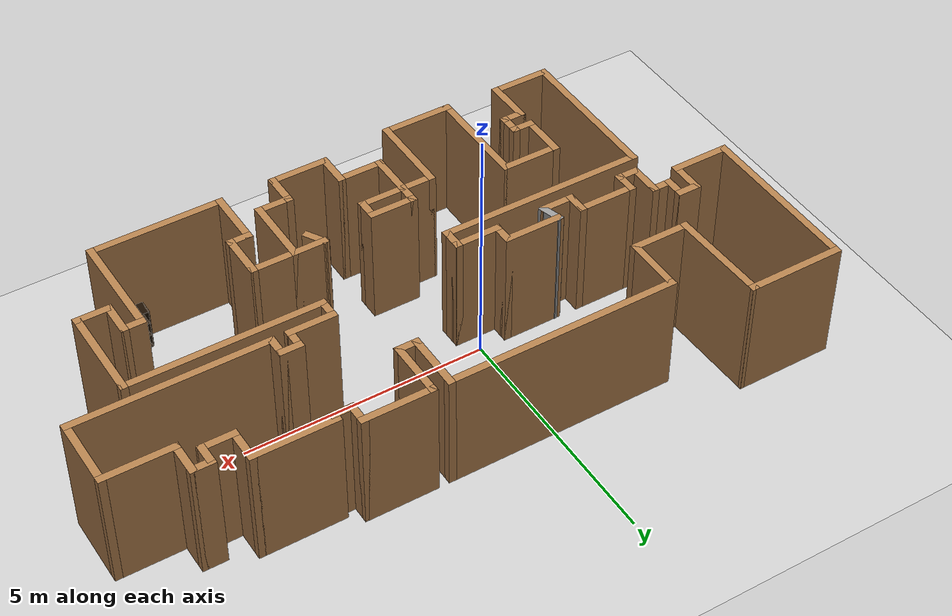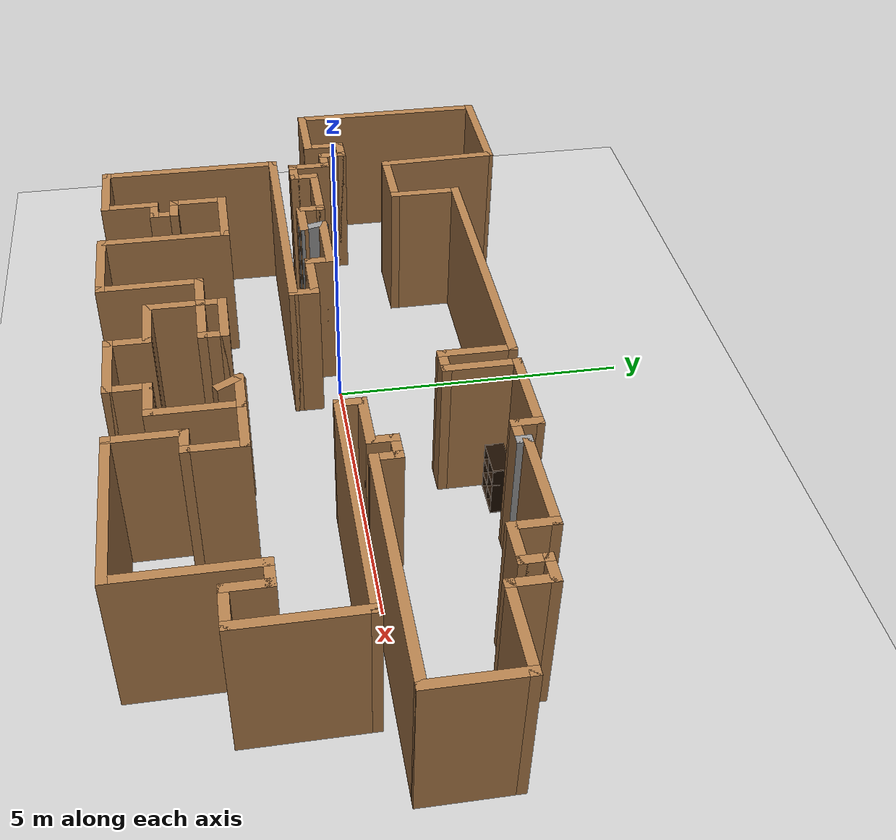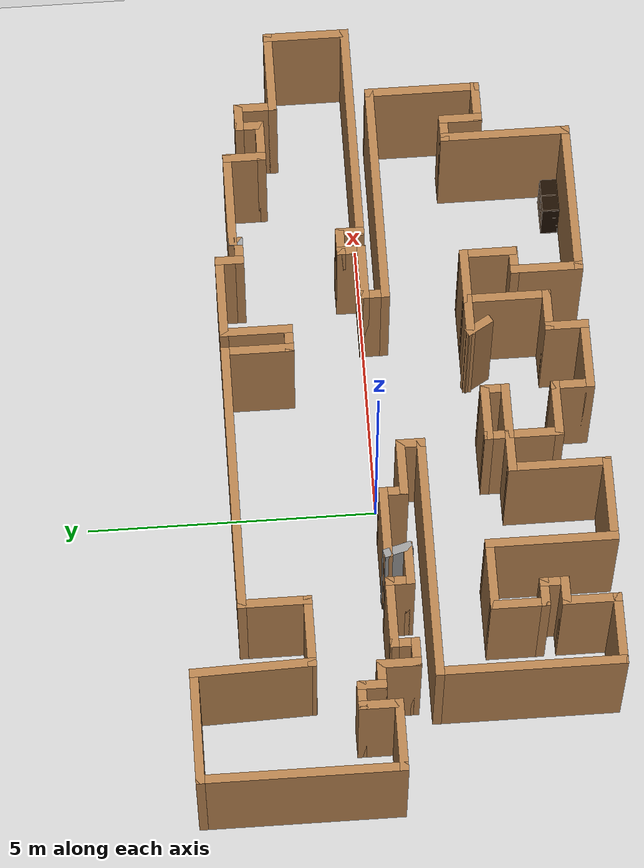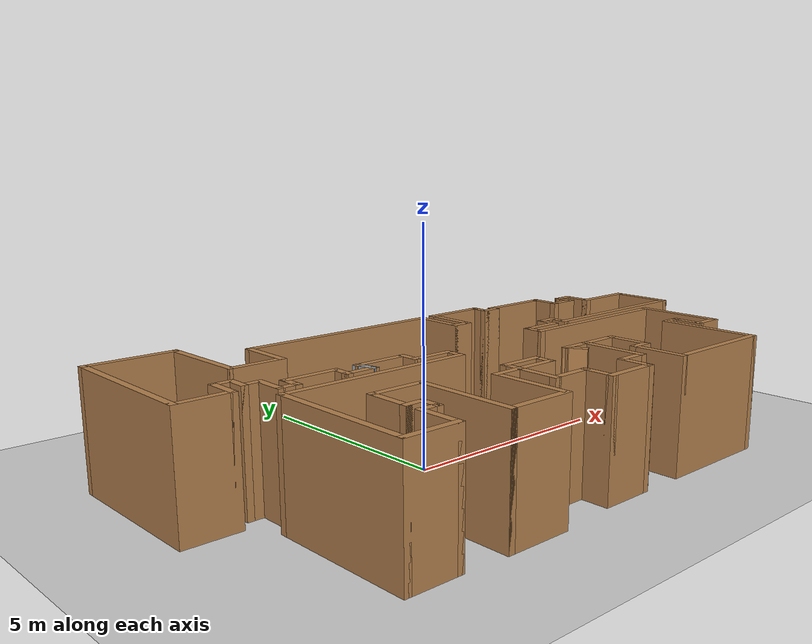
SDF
<sdf version="1.6">
 <world name="default">
  <light name="sun" type="directional">
   <pose>0 0 10 0 -0 0</pose>
   <diffuse>0.8 0.8 0.8 1</diffuse>
   <specular>0.2 0.2 0.2 1</specular>
   <attenuation>
    <range>1000</range>
    <constant>0.9</constant>
    <linear>0.01</linear>
    <quadratic>0.001</quadratic>
   </attenuation>
   <direction>-0.5 0.1 -0.9</direction>
  </light>
  <model name="ground_plane">
   <static>1</static>
   <link name="link">
    <collision name="collision">
     <geometry><plane><normal>0 0 1</normal><size>100 100</size></plane></geometry>
     <surface>
      <contact><collide_bitmask>65535</collide_bitmask></contact>
      <friction><ode><mu>100</mu><mu2>50</mu2></ode></friction>
     </surface>
    </collision>
    <visual name="visual">
     <cast_shadows>0</cast_shadows>
     <geometry><plane><normal>0 0 1</normal><size>100 100</size></plane></geometry>
     <material>
      <script><uri>file://media/materials/scripts/gazebo.material</uri><name>Gazebo/Grey</name></script>
     </material>
    </visual>
   </link>
  </model>
  <gravity>0 0 -9.8</gravity>
  <magnetic_field>6e-06 2.3e-05 -4.2e-05</magnetic_field>
  <atmosphere type="adiabatic"/>
  <physics name="default_physics" default="0" type="ode">
   <max_step_size>0.001</max_step_size>
   <real_time_factor>1</real_time_factor>
   <real_time_update_rate>1000</real_time_update_rate>
  </physics>
  <scene><ambient>0.4 0.4 0.4 1</ambient><background>0.7 0.7 0.7 1</background><shadows>1</shadows></scene>
  <audio><device>default</device></audio>
  <spherical_coordinates>
   <surface_model>EARTH_WGS84</surface_model>
   <latitude_deg>0</latitude_deg>
   <longitude_deg>0</longitude_deg>
   <elevation>0</elevation>
   <heading_deg>0</heading_deg>
  </spherical_coordinates>
  <model name="map_83">
   <pose>1.33128 -0.274002 0 0 -0 0</pose>
   <link name="Wall_0">
    <collision name="Wall_0_Collision">
     <geometry><box><size>2 0.15 2.5</size></box></geometry>
     <pose>0 0 1.25 0 -0 0</pose>
    </collision>
    <visual name="Wall_0_Visual">
     <pose>0 0 1.25 0 -0 0</pose>
     <geometry><box><size>2 0.15 2.5</size></box></geometry>
     <material>
      <script><uri>file://media/materials/scripts/gazebo.material</uri><name>Gazebo/Wood</name></script>
      <ambient>1 1 1 1</ambient>
     </material>
     <meta><layer>0</layer></meta>
    </visual>
    <pose>-5.85471 3.58172 0 0 -0 3.14159</pose>
   </link>
   <link name="Wall_1">
    <collision name="Wall_1_Collision">
     <geometry><box><size>3.5 0.15 2.5</size></box></geometry>
     <pose>0 0 1.25 0 -0 0</pose>
    </collision>
    <visual name="Wall_1_Visual">
     <pose>0 0 1.25 0 -0 0</pose>
     <geometry><box><size>3.5 0.15 2.5</size></box></geometry>
     <material>
      <script><uri>file://media/materials/scripts/gazebo.material</uri><name>Gazebo/Wood</name></script>
      <ambient>1 1 1 1</ambient>
     </material>
     <meta><layer>0</layer></meta>
    </visual>
    <pose>-6.77971 1.90672 0 0 -0 -1.5708</pose>
   </link>
   <link name="Wall_10">
    <collision name="Wall_10_Collision">
     <geometry><box><size>0.5 0.15 2.5</size></box></geometry>
     <pose>0 0 1.25 0 -0 0</pose>
    </collision>
    <visual name="Wall_10_Visual">
     <pose>0 0 1.25 0 -0 0</pose>
     <geometry><box><size>0.5 0.15 2.5</size></box></geometry>
     <material>
      <script><uri>file://media/materials/scripts/gazebo.material</uri><name>Gazebo/Wood</name></script>
      <ambient>1 1 1 1</ambient>
     </material>
     <meta><layer>0</layer></meta>
    </visual>
    <pose>-5.32971 0.656716 0 0 -0 -1.5708</pose>
   </link>
   <link name="Wall_101">
    <collision name="Wall_101_Collision">
     <geometry><box><size>0.75 0.15 2.5</size></box></geometry>
     <pose>0 0 1.25 0 -0 0</pose>
    </collision>
    <visual name="Wall_101_Visual">
     <pose>0 0 1.25 0 -0 0</pose>
     <geometry><box><size>0.75 0.15 2.5</size></box></geometry>
     <material>
      <script><uri>file://media/materials/scripts/gazebo.material</uri><name>Gazebo/Wood</name></script>
      <ambient>1 1 1 1</ambient>
     </material>
     <meta><layer>0</layer></meta>
    </visual>
    <pose>1.22971 -1.48395 0 0 -0 3.14159</pose>
   </link>
   <link name="Wall_104">
    <collision name="Wall_104_Collision">
     <geometry><box><size>0.5 0.15 2.5</size></box></geometry>
     <pose>0 0 1.25 0 -0 0</pose>
    </collision>
    <visual name="Wall_104_Visual">
     <pose>0 0 1.25 0 -0 0</pose>
     <geometry><box><size>0.5 0.15 2.5</size></box></geometry>
     <material>
      <script><uri>file://media/materials/scripts/gazebo.material</uri><name>Gazebo/Wood</name></script>
      <ambient>1 1 1 1</ambient>
     </material>
     <meta><layer>0</layer></meta>
    </visual>
    <pose>1.01721 -1.6355 0 0 -0 -1.0472</pose>
   </link>
   <link name="Wall_11">
    <collision name="Wall_11_Collision">
     <geometry><box><size>0.5 0.15 2.5</size></box></geometry>
     <pose>0 0 1.25 0 -0 0</pose>
    </collision>
    <visual name="Wall_11_Visual">
     <pose>0 0 1.25 0 -0 0</pose>
     <geometry><box><size>0.5 0.15 2.5</size></box></geometry>
     <material>
      <script><uri>file://media/materials/scripts/gazebo.material</uri><name>Gazebo/Wood</name></script>
      <ambient>1 1 1 1</ambient>
     </material>
     <meta><layer>0</layer></meta>
    </visual>
    <pose>-5.15471 0.481716 0 0 -0 0</pose>
   </link>
   <link name="Wall_12">
    <collision name="Wall_12_Collision">
     <geometry><box><size>0.75 0.15 2.5</size></box></geometry>
     <pose>0 0 1.25 0 -0 0</pose>
    </collision>
    <visual name="Wall_12_Visual">
     <pose>0 0 1.25 0 -0 0</pose>
     <geometry><box><size>0.75 0.15 2.5</size></box></geometry>
     <material>
      <script><uri>file://media/materials/scripts/gazebo.material</uri><name>Gazebo/Wood</name></script>
      <ambient>1 1 1 1</ambient>
     </material>
     <meta><layer>0</layer></meta>
    </visual>
    <pose>-4.97971 0.181717 0 0 -0 -1.5708</pose>
   </link>
   <link name="Wall_13">
    <collision name="Wall_13_Collision">
     <geometry><box><size>0.5 0.15 2.5</size></box></geometry>
     <pose>0 0 1.25 0 -0 0</pose>
    </collision>
    <visual name="Wall_13_Visual">
     <pose>0 0 1.25 0 -0 0</pose>
     <geometry><box><size>0.5 0.15 2.5</size></box></geometry>
     <material>
      <script><uri>file://media/materials/scripts/gazebo.material</uri><name>Gazebo/Wood</name></script>
      <ambient>1 1 1 1</ambient>
     </material>
     <meta><layer>0</layer></meta>
    </visual>
    <pose>-4.80471 -0.118283 0 0 -0 0</pose>
   </link>
   <link name="Wall_14">
    <collision name="Wall_14_Collision">
     <geometry><box><size>0.5 0.15 2.5</size></box></geometry>
     <pose>0 0 1.25 0 -0 0</pose>
    </collision>
    <visual name="Wall_14_Visual">
     <pose>0 0 1.25 0 -0 0</pose>
     <geometry><box><size>0.5 0.15 2.5</size></box></geometry>
     <material>
      <script><uri>file://media/materials/scripts/gazebo.material</uri><name>Gazebo/Wood</name></script>
      <ambient>1 1 1 1</ambient>
     </material>
     <meta><layer>0</layer></meta>
    </visual>
    <pose>-4.62971 0.056717 0 0 -0 1.5708</pose>
   </link>
   <link name="Wall_15">
    <collision name="Wall_15_Collision">
     <geometry><box><size>1.25 0.15 2.5</size></box></geometry>
     <pose>0 0 1.25 0 -0 0</pose>
    </collision>
    <visual name="Wall_15_Visual">
     <pose>0 0 1.25 0 -0 0</pose>
     <geometry><box><size>1.25 0.15 2.5</size></box></geometry>
     <material>
      <script><uri>file://media/materials/scripts/gazebo.material</uri><name>Gazebo/Wood</name></script>
      <ambient>1 1 1 1</ambient>
     </material>
     <meta><layer>0</layer></meta>
    </visual>
    <pose>-4.07971 0.231716 0 0 -0 0</pose>
   </link>
   <link name="Wall_16">
    <collision name="Wall_16_Collision">
     <geometry><box><size>0.5 0.15 2.5</size></box></geometry>
     <pose>0 0 1.25 0 -0 0</pose>
    </collision>
    <visual name="Wall_16_Visual">
     <pose>0 0 1.25 0 -0 0</pose>
     <geometry><box><size>0.5 0.15 2.5</size></box></geometry>
     <material>
      <script><uri>file://media/materials/scripts/gazebo.material</uri><name>Gazebo/Wood</name></script>
      <ambient>1 1 1 1</ambient>
     </material>
     <meta><layer>0</layer></meta>
    </visual>
    <pose>-3.52971 0.056717 0 0 -0 -1.5708</pose>
   </link>
   <link name="Wall_17">
    <collision name="Wall_17_Collision">
     <geometry><box><size>0.75 0.15 2.5</size></box></geometry>
     <pose>0 0 1.25 0 -0 0</pose>
    </collision>
    <visual name="Wall_17_Visual">
     <pose>0 0 1.25 0 -0 0</pose>
     <geometry><box><size>0.75 0.15 2.5</size></box></geometry>
     <material>
      <script><uri>file://media/materials/scripts/gazebo.material</uri><name>Gazebo/Wood</name></script>
      <ambient>1 1 1 1</ambient>
     </material>
     <meta><layer>0</layer></meta>
    </visual>
    <pose>-3.22971 -0.118283 0 0 -0 0</pose>
   </link>
   <link name="Wall_18">
    <collision name="Wall_18_Collision">
     <geometry><box><size>0.5 0.15 2.5</size></box></geometry>
     <pose>0 0 1.25 0 -0 0</pose>
    </collision>
    <visual name="Wall_18_Visual">
     <pose>0 0 1.25 0 -0 0</pose>
     <geometry><box><size>0.5 0.15 2.5</size></box></geometry>
     <material>
      <script><uri>file://media/materials/scripts/gazebo.material</uri><name>Gazebo/Grey</name></script>
      <ambient>1 1 1 1</ambient>
     </material>
     <meta><layer>0</layer></meta>
    </visual>
    <pose>-2.975 0.050753 0 0 -0 1.8326</pose>
   </link>
   <link name="Wall_19">
    <collision name="Wall_19_Collision">
     <geometry><box><size>1.25 0.15 2.5</size></box></geometry>
     <pose>0 0 1.25 0 -0 0</pose>
    </collision>
    <visual name="Wall_19_Visual">
     <pose>0 0 1.25 0 -0 0</pose>
     <geometry><box><size>1.25 0.15 2.5</size></box></geometry>
     <material>
      <script><uri>file://media/materials/scripts/gazebo.material</uri><name>Gazebo/Wood</name></script>
      <ambient>1 1 1 1</ambient>
     </material>
     <meta><layer>0</layer></meta>
    </visual>
    <pose>-2.47029 0.219791 0 0 -0 0</pose>
   </link>
   <link name="Wall_20">
    <collision name="Wall_20_Collision">
     <geometry><box><size>0.5 0.15 2.5</size></box></geometry>
     <pose>0 0 1.25 0 -0 0</pose>
    </collision>
    <visual name="Wall_20_Visual">
     <pose>0 0 1.25 0 -0 0</pose>
     <geometry><box><size>0.5 0.15 2.5</size></box></geometry>
     <material>
      <script><uri>file://media/materials/scripts/gazebo.material</uri><name>Gazebo/Wood</name></script>
      <ambient>1 1 1 1</ambient>
     </material>
     <meta><layer>0</layer></meta>
    </visual>
    <pose>-1.92029 0.044791 0 0 -0 -1.5708</pose>
   </link>
   <link name="Wall_21">
    <collision name="Wall_21_Collision">
     <geometry><box><size>1 0.15 2.5</size></box></geometry>
     <pose>0 0 1.25 0 -0 0</pose>
    </collision>
    <visual name="Wall_21_Visual">
     <pose>0 0 1.25 0 -0 0</pose>
     <geometry><box><size>1 0.15 2.5</size></box></geometry>
     <material>
      <script><uri>file://media/materials/scripts/gazebo.material</uri><name>Gazebo/Wood</name></script>
      <ambient>1 1 1 1</ambient>
     </material>
     <meta><layer>0</layer></meta>
    </visual>
    <pose>-1.49529 -0.130209 0 0 -0 0</pose>
   </link>
   <link name="Wall_22">
    <collision name="Wall_22_Collision">
     <geometry><box><size>0.5 0.15 2.5</size></box></geometry>
     <pose>0 0 1.25 0 -0 0</pose>
    </collision>
    <visual name="Wall_22_Visual">
     <pose>0 0 1.25 0 -0 0</pose>
     <geometry><box><size>0.5 0.15 2.5</size></box></geometry>
     <material>
      <script><uri>file://media/materials/scripts/gazebo.material</uri><name>Gazebo/Wood</name></script>
      <ambient>1 1 1 1</ambient>
     </material>
     <meta><layer>0</layer></meta>
    </visual>
    <pose>-1.07029 -0.305209 0 0 -0 -1.5708</pose>
   </link>
   <link name="Wall_23">
    <collision name="Wall_23_Collision">
     <geometry><box><size>4.25 0.15 2.5</size></box></geometry>
     <pose>0 0 1.25 0 -0 0</pose>
    </collision>
    <visual name="Wall_23_Visual">
     <pose>0 0 1.25 0 -0 0</pose>
     <geometry><box><size>4.25 0.15 2.5</size></box></geometry>
     <material>
      <script><uri>file://media/materials/scripts/gazebo.material</uri><name>Gazebo/Wood</name></script>
      <ambient>1 1 1 1</ambient>
     </material>
     <meta><layer>0</layer></meta>
    </visual>
    <pose>-3.12029 -0.48021 0 0 -0 3.14159</pose>
   </link>
   <link name="Wall_24">
    <collision name="Wall_24_Collision">
     <geometry><box><size>3.20374 0.15 2.5</size></box></geometry>
     <pose>0 0 1.25 0 -0 0</pose>
    </collision>
    <visual name="Wall_24_Visual">
     <pose>0 0 1.25 0 -0 0</pose>
     <geometry><box><size>3.20374 0.15 2.5</size></box></geometry>
     <material>
      <script><uri>file://media/materials/scripts/gazebo.material</uri><name>Gazebo/Wood</name></script>
      <ambient>1 1 1 1</ambient>
     </material>
     <meta><layer>0</layer></meta>
    </visual>
    <pose>-5.17029 -2.00708 0 0 -0 -1.5708</pose>
   </link>
   <link name="Wall_30">
    <collision name="Wall_30_Collision">
     <geometry><box><size>1.25 0.15 2.5</size></box></geometry>
     <pose>0 0 1.25 0 -0 0</pose>
    </collision>
    <visual name="Wall_30_Visual">
     <pose>0 0 1.25 0 -0 0</pose>
     <geometry><box><size>1.25 0.15 2.5</size></box></geometry>
     <material>
      <script><uri>file://media/materials/scripts/gazebo.material</uri><name>Gazebo/Wood</name></script>
      <ambient>1 1 1 1</ambient>
     </material>
     <meta><layer>0</layer></meta>
    </visual>
    <pose>-4.62029 -3.53395 0 0 -0 0</pose>
   </link>
   <link name="Wall_31">
    <collision name="Wall_31_Collision">
     <geometry><box><size>1 0.15 2.5</size></box></geometry>
     <pose>0 0 1.25 0 -0 0</pose>
    </collision>
    <visual name="Wall_31_Visual">
     <pose>0 0 1.25 0 -0 0</pose>
     <geometry><box><size>1 0.15 2.5</size></box></geometry>
     <material>
      <script><uri>file://media/materials/scripts/gazebo.material</uri><name>Gazebo/Wood</name></script>
      <ambient>1 1 1 1</ambient>
     </material>
     <meta><layer>0</layer></meta>
    </visual>
    <pose>-4.07029 -3.10895 0 0 -0 1.5708</pose>
   </link>
   <link name="Wall_32">
    <collision name="Wall_32_Collision">
     <geometry><box><size>0.5 0.15 2.5</size></box></geometry>
     <pose>0 0 1.25 0 -0 0</pose>
    </collision>
    <visual name="Wall_32_Visual">
     <pose>0 0 1.25 0 -0 0</pose>
     <geometry><box><size>0.5 0.15 2.5</size></box></geometry>
     <material>
      <script><uri>file://media/materials/scripts/gazebo.material</uri><name>Gazebo/Wood</name></script>
      <ambient>1 1 1 1</ambient>
     </material>
     <meta><layer>0</layer></meta>
    </visual>
    <pose>-3.89529 -2.68395 0 0 -0 0</pose>
   </link>
   <link name="Wall_33">
    <collision name="Wall_33_Collision">
     <geometry><box><size>0.5 0.15 2.5</size></box></geometry>
     <pose>0 0 1.25 0 -0 0</pose>
    </collision>
    <visual name="Wall_33_Visual">
     <pose>0 0 1.25 0 -0 0</pose>
     <geometry><box><size>0.5 0.15 2.5</size></box></geometry>
     <material>
      <script><uri>file://media/materials/scripts/gazebo.material</uri><name>Gazebo/Wood</name></script>
      <ambient>1 1 1 1</ambient>
     </material>
     <meta><layer>0</layer></meta>
    </visual>
    <pose>-3.72029 -2.50895 0 0 -0 1.5708</pose>
   </link>
   <link name="Wall_34">
    <collision name="Wall_34_Collision">
     <geometry><box><size>0.5 0.15 2.5</size></box></geometry>
     <pose>0 0 1.25 0 -0 0</pose>
    </collision>
    <visual name="Wall_34_Visual">
     <pose>0 0 1.25 0 -0 0</pose>
     <geometry><box><size>0.5 0.15 2.5</size></box></geometry>
     <material>
      <script><uri>file://media/materials/scripts/gazebo.material</uri><name>Gazebo/Wood</name></script>
      <ambient>1 1 1 1</ambient>
     </material>
     <meta><layer>0</layer></meta>
    </visual>
    <pose>-3.89529 -2.33395 0 0 -0 3.14159</pose>
   </link>
   <link name="Wall_35">
    <collision name="Wall_35_Collision">
     <geometry><box><size>1 0.15 2.5</size></box></geometry>
     <pose>0 0 1.25 0 -0 0</pose>
    </collision>
    <visual name="Wall_35_Visual">
     <pose>0 0 1.25 0 -0 0</pose>
     <geometry><box><size>1 0.15 2.5</size></box></geometry>
     <material>
      <script><uri>file://media/materials/scripts/gazebo.material</uri><name>Gazebo/Wood</name></script>
      <ambient>1 1 1 1</ambient>
     </material>
     <meta><layer>0</layer></meta>
    </visual>
    <pose>-4.07029 -1.90895 0 0 -0 1.5708</pose>
   </link>
   <link name="Wall_36">
    <collision name="Wall_36_Collision">
     <geometry><box><size>1.25 0.15 2.5</size></box></geometry>
     <pose>0 0 1.25 0 -0 0</pose>
    </collision>
    <visual name="Wall_36_Visual">
     <pose>0 0 1.25 0 -0 0</pose>
     <geometry><box><size>1.25 0.15 2.5</size></box></geometry>
     <material>
      <script><uri>file://media/materials/scripts/gazebo.material</uri><name>Gazebo/Wood</name></script>
      <ambient>1 1 1 1</ambient>
     </material>
     <meta><layer>0</layer></meta>
    </visual>
    <pose>-3.52029 -1.48395 0 0 -0 0</pose>
   </link>
   <link name="Wall_37">
    <collision name="Wall_37_Collision">
     <geometry><box><size>2.25 0.15 2.5</size></box></geometry>
     <pose>0 0 1.25 0 -0 0</pose>
    </collision>
    <visual name="Wall_37_Visual">
     <pose>0 0 1.25 0 -0 0</pose>
     <geometry><box><size>2.25 0.15 2.5</size></box></geometry>
     <material>
      <script><uri>file://media/materials/scripts/gazebo.material</uri><name>Gazebo/Wood</name></script>
      <ambient>1 1 1 1</ambient>
     </material>
     <meta><layer>0</layer></meta>
    </visual>
    <pose>-2.97029 -2.53395 0 0 -0 -1.5708</pose>
   </link>
   <link name="Wall_38">
    <collision name="Wall_38_Collision">
     <geometry><box><size>1.5 0.15 2.5</size></box></geometry>
     <pose>0 0 1.25 0 -0 0</pose>
    </collision>
    <visual name="Wall_38_Visual">
     <pose>0 0 1.25 0 -0 0</pose>
     <geometry><box><size>1.5 0.15 2.5</size></box></geometry>
     <material>
      <script><uri>file://media/materials/scripts/gazebo.material</uri><name>Gazebo/Wood</name></script>
      <ambient>1 1 1 1</ambient>
     </material>
     <meta><layer>0</layer></meta>
    </visual>
    <pose>-2.29529 -3.58395 0 0 -0 0</pose>
   </link>
   <link name="Wall_42">
    <collision name="Wall_42_Collision">
     <geometry><box><size>1.75 0.15 2.5</size></box></geometry>
     <pose>0 0 1.25 0 -0 0</pose>
    </collision>
    <visual name="Wall_42_Visual">
     <pose>0 0 1.25 0 -0 0</pose>
     <geometry><box><size>1.75 0.15 2.5</size></box></geometry>
     <material>
      <script><uri>file://media/materials/scripts/gazebo.material</uri><name>Gazebo/Wood</name></script>
      <ambient>1 1 1 1</ambient>
     </material>
     <meta><layer>0</layer></meta>
    </visual>
    <pose>-1.62029 -2.78395 0 0 -0 1.5708</pose>
   </link>
   <link name="Wall_43">
    <collision name="Wall_43_Collision">
     <geometry><box><size>0.75 0.15 2.5</size></box></geometry>
     <pose>0 0 1.25 0 -0 0</pose>
    </collision>
    <visual name="Wall_43_Visual">
     <pose>0 0 1.25 0 -0 0</pose>
     <geometry><box><size>0.75 0.15 2.5</size></box></geometry>
     <material>
      <script><uri>file://media/materials/scripts/gazebo.material</uri><name>Gazebo/Wood</name></script>
      <ambient>1 1 1 1</ambient>
     </material>
     <meta><layer>0</layer></meta>
    </visual>
    <pose>-1.32029 -1.98395 0 0 -0 0</pose>
   </link>
   <link name="Wall_44">
    <collision name="Wall_44_Collision">
     <geometry><box><size>0.5 0.15 2.5</size></box></geometry>
     <pose>0 0 1.25 0 -0 0</pose>
    </collision>
    <visual name="Wall_44_Visual">
     <pose>0 0 1.25 0 -0 0</pose>
     <geometry><box><size>0.5 0.15 2.5</size></box></geometry>
     <material>
      <script><uri>file://media/materials/scripts/gazebo.material</uri><name>Gazebo/Wood</name></script>
      <ambient>1 1 1 1</ambient>
     </material>
     <meta><layer>0</layer></meta>
    </visual>
    <pose>-1.02029 -1.80895 0 0 -0 1.5708</pose>
   </link>
   <link name="Wall_45">
    <collision name="Wall_45_Collision">
     <geometry><box><size>1 0.15 2.5</size></box></geometry>
     <pose>0 0 1.25 0 -0 0</pose>
    </collision>
    <visual name="Wall_45_Visual">
     <pose>0 0 1.25 0 -0 0</pose>
     <geometry><box><size>1 0.15 2.5</size></box></geometry>
     <material>
      <script><uri>file://media/materials/scripts/gazebo.material</uri><name>Gazebo/Wood</name></script>
      <ambient>1 1 1 1</ambient>
     </material>
     <meta><layer>0</layer></meta>
    </visual>
    <pose>-0.595293 -1.63395 0 0 -0 0</pose>
   </link>
   <link name="Wall_50">
    <collision name="Wall_50_Collision">
     <geometry><box><size>0.5 0.15 2.5</size></box></geometry>
     <pose>0 0 1.25 0 -0 0</pose>
    </collision>
    <visual name="Wall_50_Visual">
     <pose>0 0 1.25 0 -0 0</pose>
     <geometry><box><size>0.5 0.15 2.5</size></box></geometry>
     <material>
      <script><uri>file://media/materials/scripts/gazebo.material</uri><name>Gazebo/Wood</name></script>
      <ambient>1 1 1 1</ambient>
     </material>
     <meta><layer>0</layer></meta>
    </visual>
    <pose>-0.170293 -1.80895 0 0 -0 -1.5708</pose>
   </link>
   <link name="Wall_51">
    <collision name="Wall_51_Collision">
     <geometry><box><size>1 0.15 2.5</size></box></geometry>
     <pose>0 0 1.25 0 -0 0</pose>
    </collision>
    <visual name="Wall_51_Visual">
     <pose>0 0 1.25 0 -0 0</pose>
     <geometry><box><size>1 0.15 2.5</size></box></geometry>
     <material>
      <script><uri>file://media/materials/scripts/gazebo.material</uri><name>Gazebo/Wood</name></script>
      <ambient>1 1 1 1</ambient>
     </material>
     <meta><layer>0</layer></meta>
    </visual>
    <pose>-0.595293 -1.98395 0 0 -0 3.14159</pose>
   </link>
   <link name="Wall_52">
    <collision name="Wall_52_Collision">
     <geometry><box><size>1 0.15 2.5</size></box></geometry>
     <pose>0 0 1.25 0 -0 0</pose>
    </collision>
    <visual name="Wall_52_Visual">
     <pose>0 0 1.25 0 -0 0</pose>
     <geometry><box><size>1 0.15 2.5</size></box></geometry>
     <material>
      <script><uri>file://media/materials/scripts/gazebo.material</uri><name>Gazebo/Wood</name></script>
      <ambient>1 1 1 1</ambient>
     </material>
     <meta><layer>0</layer></meta>
    </visual>
    <pose>-1.02029 -2.40895 0 0 -0 -1.5708</pose>
   </link>
   <link name="Wall_53">
    <collision name="Wall_53_Collision">
     <geometry><box><size>1 0.15 2.5</size></box></geometry>
     <pose>0 0 1.25 0 -0 0</pose>
    </collision>
    <visual name="Wall_53_Visual">
     <pose>0 0 1.25 0 -0 0</pose>
     <geometry><box><size>1 0.15 2.5</size></box></geometry>
     <material>
      <script><uri>file://media/materials/scripts/gazebo.material</uri><name>Gazebo/Wood</name></script>
      <ambient>1 1 1 1</ambient>
     </material>
     <meta><layer>0</layer></meta>
    </visual>
    <pose>-0.595293 -2.83395 0 0 -0 0</pose>
   </link>
   <link name="Wall_54">
    <collision name="Wall_54_Collision">
     <geometry><box><size>0.75 0.15 2.5</size></box></geometry>
     <pose>0 0 1.25 0 -0 0</pose>
    </collision>
    <visual name="Wall_54_Visual">
     <pose>0 0 1.25 0 -0 0</pose>
     <geometry><box><size>0.75 0.15 2.5</size></box></geometry>
     <material>
      <script><uri>file://media/materials/scripts/gazebo.material</uri><name>Gazebo/Wood</name></script>
      <ambient>1 1 1 1</ambient>
     </material>
     <meta><layer>0</layer></meta>
    </visual>
    <pose>-0.170293 -3.13395 0 0 -0 -1.5708</pose>
   </link>
   <link name="Wall_55">
    <collision name="Wall_55_Collision">
     <geometry><box><size>1.25 0.15 2.5</size></box></geometry>
     <pose>0 0 1.25 0 -0 0</pose>
    </collision>
    <visual name="Wall_55_Visual">
     <pose>0 0 1.25 0 -0 0</pose>
     <geometry><box><size>1.25 0.15 2.5</size></box></geometry>
     <material>
      <script><uri>file://media/materials/scripts/gazebo.material</uri><name>Gazebo/Wood</name></script>
      <ambient>1 1 1 1</ambient>
     </material>
     <meta><layer>0</layer></meta>
    </visual>
    <pose>0.379707 -3.43395 0 0 -0 0</pose>
   </link>
   <link name="Wall_56">
    <collision name="Wall_56_Collision">
     <geometry><box><size>0.75 0.15 2.5</size></box></geometry>
     <pose>0 0 1.25 0 -0 0</pose>
    </collision>
    <visual name="Wall_56_Visual">
     <pose>0 0 1.25 0 -0 0</pose>
     <geometry><box><size>0.75 0.15 2.5</size></box></geometry>
     <material>
      <script><uri>file://media/materials/scripts/gazebo.material</uri><name>Gazebo/Wood</name></script>
      <ambient>1 1 1 1</ambient>
     </material>
     <meta><layer>0</layer></meta>
    </visual>
    <pose>0.929707 -3.13395 0 0 -0 1.5708</pose>
   </link>
   <link name="Wall_57">
    <collision name="Wall_57_Collision">
     <geometry><box><size>0.75 0.15 2.5</size></box></geometry>
     <pose>0 0 1.25 0 -0 0</pose>
    </collision>
    <visual name="Wall_57_Visual">
     <pose>0 0 1.25 0 -0 0</pose>
     <geometry><box><size>0.75 0.15 2.5</size></box></geometry>
     <material>
      <script><uri>file://media/materials/scripts/gazebo.material</uri><name>Gazebo/Wood</name></script>
      <ambient>1 1 1 1</ambient>
     </material>
     <meta><layer>0</layer></meta>
    </visual>
    <pose>1.22971 -2.83395 0 0 -0 0</pose>
   </link>
   <link name="Wall_58">
    <collision name="Wall_58_Collision">
     <geometry><box><size>1.5 0.15 2.5</size></box></geometry>
     <pose>0 0 1.25 0 -0 0</pose>
    </collision>
    <visual name="Wall_58_Visual">
     <pose>0 0 1.25 0 -0 0</pose>
     <geometry><box><size>1.5 0.15 2.5</size></box></geometry>
     <material>
      <script><uri>file://media/materials/scripts/gazebo.material</uri><name>Gazebo/Wood</name></script>
      <ambient>1 1 1 1</ambient>
     </material>
     <meta><layer>0</layer></meta>
    </visual>
    <pose>1.52971 -2.15895 0 0 -0 1.5708</pose>
   </link>
   <link name="Wall_59">
    <collision name="Wall_59_Collision">
     <geometry><box><size>1 0.15 2.5</size></box></geometry>
     <pose>0 0 1.25 0 -0 0</pose>
    </collision>
    <visual name="Wall_59_Visual">
     <pose>0 0 1.25 0 -0 0</pose>
     <geometry><box><size>1 0.15 2.5</size></box></geometry>
     <material>
      <script><uri>file://media/materials/scripts/gazebo.material</uri><name>Gazebo/Wood</name></script>
      <ambient>1 1 1 1</ambient>
     </material>
     <meta><layer>0</layer></meta>
    </visual>
    <pose>1.95471 -1.48395 0 0 -0 0</pose>
   </link>
   <link name="Wall_60">
    <collision name="Wall_60_Collision">
     <geometry><box><size>1 0.15 2.5</size></box></geometry>
     <pose>0 0 1.25 0 -0 0</pose>
    </collision>
    <visual name="Wall_60_Visual">
     <pose>0 0 1.25 0 -0 0</pose>
     <geometry><box><size>1 0.15 2.5</size></box></geometry>
     <material>
      <script><uri>file://media/materials/scripts/gazebo.material</uri><name>Gazebo/Wood</name></script>
      <ambient>1 1 1 1</ambient>
     </material>
     <meta><layer>0</layer></meta>
    </visual>
    <pose>2.37971 -1.90895 0 0 -0 -1.5708</pose>
   </link>
   <link name="Wall_61">
    <collision name="Wall_61_Collision">
     <geometry><box><size>0.5 0.15 2.5</size></box></geometry>
     <pose>0 0 1.25 0 -0 0</pose>
    </collision>
    <visual name="Wall_61_Visual">
     <pose>0 0 1.25 0 -0 0</pose>
     <geometry><box><size>0.5 0.15 2.5</size></box></geometry>
     <material>
      <script><uri>file://media/materials/scripts/gazebo.material</uri><name>Gazebo/Wood</name></script>
      <ambient>1 1 1 1</ambient>
     </material>
     <meta><layer>0</layer></meta>
    </visual>
    <pose>2.20471 -2.33395 0 0 -0 3.14159</pose>
   </link>
   <link name="Wall_62">
    <collision name="Wall_62_Collision">
     <geometry><box><size>1.25 0.15 2.5</size></box></geometry>
     <pose>0 0 1.25 0 -0 0</pose>
    </collision>
    <visual name="Wall_62_Visual">
     <pose>0 0 1.25 0 -0 0</pose>
     <geometry><box><size>1.25 0.15 2.5</size></box></geometry>
     <material>
      <script><uri>file://media/materials/scripts/gazebo.material</uri><name>Gazebo/Wood</name></script>
      <ambient>1 1 1 1</ambient>
     </material>
     <meta><layer>0</layer></meta>
    </visual>
    <pose>2.02971 -2.88395 0 0 -0 -1.5708</pose>
   </link>
   <link name="Wall_63">
    <collision name="Wall_63_Collision">
     <geometry><box><size>2.75 0.15 2.5</size></box></geometry>
     <pose>0 0 1.25 0 -0 0</pose>
    </collision>
    <visual name="Wall_63_Visual">
     <pose>0 0 1.25 0 -0 0</pose>
     <geometry><box><size>2.75 0.15 2.5</size></box></geometry>
     <material>
      <script><uri>file://media/materials/scripts/gazebo.material</uri><name>Gazebo/Wood</name></script>
      <ambient>1 1 1 1</ambient>
     </material>
     <meta><layer>0</layer></meta>
    </visual>
    <pose>3.32971 -3.43395 0 0 -0 0</pose>
   </link>
   <link name="Wall_64">
    <collision name="Wall_64_Collision">
     <geometry><box><size>2.25 0.15 2.5</size></box></geometry>
     <pose>0 0 1.25 0 -0 0</pose>
    </collision>
    <visual name="Wall_64_Visual">
     <pose>0 0 1.25 0 -0 0</pose>
     <geometry><box><size>2.25 0.15 2.5</size></box></geometry>
     <material>
      <script><uri>file://media/materials/scripts/gazebo.material</uri><name>Gazebo/Wood</name></script>
      <ambient>1 1 1 1</ambient>
     </material>
     <meta><layer>0</layer></meta>
    </visual>
    <pose>4.62971 -2.38395 0 0 -0 1.5708</pose>
   </link>
   <link name="Wall_65">
    <collision name="Wall_65_Collision">
     <geometry><box><size>0.5 0.15 2.5</size></box></geometry>
     <pose>0 0 1.25 0 -0 0</pose>
    </collision>
    <visual name="Wall_65_Visual">
     <pose>0 0 1.25 0 -0 0</pose>
     <geometry><box><size>0.5 0.15 2.5</size></box></geometry>
     <material>
      <script><uri>file://media/materials/scripts/gazebo.material</uri><name>Gazebo/Wood</name></script>
      <ambient>1 1 1 1</ambient>
     </material>
     <meta><layer>0</layer></meta>
    </visual>
    <pose>4.80471 -1.33395 0 0 -0 0</pose>
   </link>
   <link name="Wall_66">
    <collision name="Wall_66_Collision">
     <geometry><box><size>0.75 0.15 2.5</size></box></geometry>
     <pose>0 0 1.25 0 -0 0</pose>
    </collision>
    <visual name="Wall_66_Visual">
     <pose>0 0 1.25 0 -0 0</pose>
     <geometry><box><size>0.75 0.15 2.5</size></box></geometry>
     <material>
      <script><uri>file://media/materials/scripts/gazebo.material</uri><name>Gazebo/Wood</name></script>
      <ambient>1 1 1 1</ambient>
     </material>
     <meta><layer>0</layer></meta>
    </visual>
    <pose>4.97971 -1.63395 0 0 -0 -1.5708</pose>
   </link>
   <link name="Wall_67">
    <collision name="Wall_67_Collision">
     <geometry><box><size>0.75 0.15 2.5</size></box></geometry>
     <pose>0 0 1.25 0 -0 0</pose>
    </collision>
    <visual name="Wall_67_Visual">
     <pose>0 0 1.25 0 -0 0</pose>
     <geometry><box><size>0.75 0.15 2.5</size></box></geometry>
     <material>
      <script><uri>file://media/materials/scripts/gazebo.material</uri><name>Gazebo/Wood</name></script>
      <ambient>1 1 1 1</ambient>
     </material>
     <meta><layer>0</layer></meta>
    </visual>
    <pose>5.27971 -1.93395 0 0 -0 0</pose>
   </link>
   <link name="Wall_68">
    <collision name="Wall_68_Collision">
     <geometry><box><size>2 0.15 2.5</size></box></geometry>
     <pose>0 0 1.25 0 -0 0</pose>
    </collision>
    <visual name="Wall_68_Visual">
     <pose>0 0 1.25 0 -0 0</pose>
     <geometry><box><size>2 0.15 2.5</size></box></geometry>
     <material>
      <script><uri>file://media/materials/scripts/gazebo.material</uri><name>Gazebo/Wood</name></script>
      <ambient>1 1 1 1</ambient>
     </material>
     <meta><layer>0</layer></meta>
    </visual>
    <pose>5.57971 -1.00895 0 0 -0 1.5708</pose>
   </link>
   <link name="Wall_69">
    <collision name="Wall_69_Collision">
     <geometry><box><size>4 0.15 2.5</size></box></geometry>
     <pose>0 0 1.25 0 -0 0</pose>
    </collision>
    <visual name="Wall_69_Visual">
     <pose>0 0 1.25 0 -0 0</pose>
     <geometry><box><size>4 0.15 2.5</size></box></geometry>
     <material>
      <script><uri>file://media/materials/scripts/gazebo.material</uri><name>Gazebo/Wood</name></script>
      <ambient>1 1 1 1</ambient>
     </material>
     <meta><layer>0</layer></meta>
    </visual>
    <pose>3.65471 -0.083948 0 0 -0 3.14159</pose>
   </link>
   <link name="Wall_7">
    <collision name="Wall_7_Collision">
     <geometry><box><size>1.25 0.15 2.5</size></box></geometry>
     <pose>0 0 1.25 0 -0 0</pose>
    </collision>
    <visual name="Wall_7_Visual">
     <pose>0 0 1.25 0 -0 0</pose>
     <geometry><box><size>1.25 0.15 2.5</size></box></geometry>
     <material>
      <script><uri>file://media/materials/scripts/gazebo.material</uri><name>Gazebo/Wood</name></script>
      <ambient>1 1 1 1</ambient>
     </material>
     <meta><layer>0</layer></meta>
    </visual>
    <pose>-6.22971 0.231716 0 0 -0 0</pose>
   </link>
   <link name="Wall_72">
    <collision name="Wall_72_Collision">
     <geometry><box><size>0.5 0.15 2.5</size></box></geometry>
     <pose>0 0 1.25 0 -0 0</pose>
    </collision>
    <visual name="Wall_72_Visual">
     <pose>0 0 1.25 0 -0 0</pose>
     <geometry><box><size>0.5 0.15 2.5</size></box></geometry>
     <material>
      <script><uri>file://media/materials/scripts/gazebo.material</uri><name>Gazebo/Wood</name></script>
      <ambient>1 1 1 1</ambient>
     </material>
     <meta><layer>0</layer></meta>
    </visual>
    <pose>1.72971 0.091052 0 0 -0 1.5708</pose>
   </link>
   <link name="Wall_73">
    <collision name="Wall_73_Collision">
     <geometry><box><size>1 0.15 2.5</size></box></geometry>
     <pose>0 0 1.25 0 -0 0</pose>
    </collision>
    <visual name="Wall_73_Visual">
     <pose>0 0 1.25 0 -0 0</pose>
     <geometry><box><size>1 0.15 2.5</size></box></geometry>
     <material>
      <script><uri>file://media/materials/scripts/gazebo.material</uri><name>Gazebo/Wood</name></script>
      <ambient>1 1 1 1</ambient>
     </material>
     <meta><layer>0</layer></meta>
    </visual>
    <pose>2.15471 0.266052 0 0 -0 0</pose>
   </link>
   <link name="Wall_74">
    <collision name="Wall_74_Collision">
     <geometry><box><size>0.5 0.15 2.5</size></box></geometry>
     <pose>0 0 1.25 0 -0 0</pose>
    </collision>
    <visual name="Wall_74_Visual">
     <pose>0 0 1.25 0 -0 0</pose>
     <geometry><box><size>0.5 0.15 2.5</size></box></geometry>
     <material>
      <script><uri>file://media/materials/scripts/gazebo.material</uri><name>Gazebo/Wood</name></script>
      <ambient>1 1 1 1</ambient>
     </material>
     <meta><layer>0</layer></meta>
    </visual>
    <pose>2.57971 0.441052 0 0 -0 1.5708</pose>
   </link>
   <link name="Wall_75">
    <collision name="Wall_75_Collision">
     <geometry><box><size>0.5 0.15 2.5</size></box></geometry>
     <pose>0 0 1.25 0 -0 0</pose>
    </collision>
    <visual name="Wall_75_Visual">
     <pose>0 0 1.25 0 -0 0</pose>
     <geometry><box><size>0.5 0.15 2.5</size></box></geometry>
     <material>
      <script><uri>file://media/materials/scripts/gazebo.material</uri><name>Gazebo/Wood</name></script>
      <ambient>1 1 1 1</ambient>
     </material>
     <meta><layer>0</layer></meta>
    </visual>
    <pose>2.75471 0.616052 0 0 -0 0</pose>
   </link>
   <link name="Wall_76">
    <collision name="Wall_76_Collision">
     <geometry><box><size>0.5 0.15 2.5</size></box></geometry>
     <pose>0 0 1.25 0 -0 0</pose>
    </collision>
    <visual name="Wall_76_Visual">
     <pose>0 0 1.25 0 -0 0</pose>
     <geometry><box><size>0.5 0.15 2.5</size></box></geometry>
     <material>
      <script><uri>file://media/materials/scripts/gazebo.material</uri><name>Gazebo/Wood</name></script>
      <ambient>1 1 1 1</ambient>
     </material>
     <meta><layer>0</layer></meta>
    </visual>
    <pose>2.92971 0.441052 0 0 -0 -1.5708</pose>
   </link>
   <link name="Wall_77">
    <collision name="Wall_77_Collision">
     <geometry><box><size>4 0.15 2.5</size></box></geometry>
     <pose>0 0 1.25 0 -0 0</pose>
    </collision>
    <visual name="Wall_77_Visual">
     <pose>0 0 1.25 0 -0 0</pose>
     <geometry><box><size>4 0.15 2.5</size></box></geometry>
     <material>
      <script><uri>file://media/materials/scripts/gazebo.material</uri><name>Gazebo/Wood</name></script>
      <ambient>1 1 1 1</ambient>
     </material>
     <meta><layer>0</layer></meta>
    </visual>
    <pose>4.85471 0.266052 0 0 -0 0</pose>
   </link>
   <link name="Wall_78">
    <collision name="Wall_78_Collision">
     <geometry><box><size>1.5 0.15 2.5</size></box></geometry>
     <pose>0 0 1.25 0 -0 0</pose>
    </collision>
    <visual name="Wall_78_Visual">
     <pose>0 0 1.25 0 -0 0</pose>
     <geometry><box><size>1.5 0.15 2.5</size></box></geometry>
     <material>
      <script><uri>file://media/materials/scripts/gazebo.material</uri><name>Gazebo/Wood</name></script>
      <ambient>1 1 1 1</ambient>
     </material>
     <meta><layer>0</layer></meta>
    </visual>
    <pose>6.77971 0.941052 0 0 -0 1.5708</pose>
   </link>
   <link name="Wall_79">
    <collision name="Wall_79_Collision">
     <geometry><box><size>1.5 0.15 2.5</size></box></geometry>
     <pose>0 0 1.25 0 -0 0</pose>
    </collision>
    <visual name="Wall_79_Visual">
     <pose>0 0 1.25 0 -0 0</pose>
     <geometry><box><size>1.5 0.15 2.5</size></box></geometry>
     <material>
      <script><uri>file://media/materials/scripts/gazebo.material</uri><name>Gazebo/Wood</name></script>
      <ambient>1 1 1 1</ambient>
     </material>
     <meta><layer>0</layer></meta>
    </visual>
    <pose>6.10471 1.61605 0 0 -0 3.14159</pose>
   </link>
   <link name="Wall_8">
    <collision name="Wall_8_Collision">
     <geometry><box><size>0.75 0.15 2.5</size></box></geometry>
     <pose>0 0 1.25 0 -0 0</pose>
    </collision>
    <visual name="Wall_8_Visual">
     <pose>0 0 1.25 0 -0 0</pose>
     <geometry><box><size>0.75 0.15 2.5</size></box></geometry>
     <material>
      <script><uri>file://media/materials/scripts/gazebo.material</uri><name>Gazebo/Wood</name></script>
      <ambient>1 1 1 1</ambient>
     </material>
     <meta><layer>0</layer></meta>
    </visual>
    <pose>-5.67971 0.531716 0 0 -0 1.5708</pose>
   </link>
   <link name="Wall_80">
    <collision name="Wall_80_Collision">
     <geometry><box><size>0.75 0.15 2.5</size></box></geometry>
     <pose>0 0 1.25 0 -0 0</pose>
    </collision>
    <visual name="Wall_80_Visual">
     <pose>0 0 1.25 0 -0 0</pose>
     <geometry><box><size>0.75 0.15 2.5</size></box></geometry>
     <material>
      <script><uri>file://media/materials/scripts/gazebo.material</uri><name>Gazebo/Wood</name></script>
      <ambient>1 1 1 1</ambient>
     </material>
     <meta><layer>0</layer></meta>
    </visual>
    <pose>5.42971 1.91605 0 0 -0 1.5708</pose>
   </link>
   <link name="Wall_81">
    <collision name="Wall_81_Collision">
     <geometry><box><size>0.5 0.15 2.5</size></box></geometry>
     <pose>0 0 1.25 0 -0 0</pose>
    </collision>
    <visual name="Wall_81_Visual">
     <pose>0 0 1.25 0 -0 0</pose>
     <geometry><box><size>0.5 0.15 2.5</size></box></geometry>
     <material>
      <script><uri>file://media/materials/scripts/gazebo.material</uri><name>Gazebo/Wood</name></script>
      <ambient>1 1 1 1</ambient>
     </material>
     <meta><layer>0</layer></meta>
    </visual>
    <pose>5.25471 2.21605 0 0 -0 3.14159</pose>
   </link>
   <link name="Wall_82">
    <collision name="Wall_82_Collision">
     <geometry><box><size>0.5 0.15 2.5</size></box></geometry>
     <pose>0 0 1.25 0 -0 0</pose>
    </collision>
    <visual name="Wall_82_Visual">
     <pose>0 0 1.25 0 -0 0</pose>
     <geometry><box><size>0.5 0.15 2.5</size></box></geometry>
     <material>
      <script><uri>file://media/materials/scripts/gazebo.material</uri><name>Gazebo/Wood</name></script>
      <ambient>1 1 1 1</ambient>
     </material>
     <meta><layer>0</layer></meta>
    </visual>
    <pose>5.07971 2.04105 0 0 -0 -1.5708</pose>
   </link>
   <link name="Wall_83">
    <collision name="Wall_83_Collision">
     <geometry><box><size>0.75 0.15 2.5</size></box></geometry>
     <pose>0 0 1.25 0 -0 0</pose>
    </collision>
    <visual name="Wall_83_Visual">
     <pose>0 0 1.25 0 -0 0</pose>
     <geometry><box><size>0.75 0.15 2.5</size></box></geometry>
     <material>
      <script><uri>file://media/materials/scripts/gazebo.material</uri><name>Gazebo/Wood</name></script>
      <ambient>1 1 1 1</ambient>
     </material>
     <meta><layer>0</layer></meta>
    </visual>
    <pose>4.77971 1.86605 0 0 -0 3.14159</pose>
   </link>
   <link name="Wall_84">
    <collision name="Wall_84_Collision">
     <geometry><box><size>0.75 0.15 2.5</size></box></geometry>
     <pose>0 0 1.25 0 -0 0</pose>
    </collision>
    <visual name="Wall_84_Visual">
     <pose>0 0 1.25 0 -0 0</pose>
     <geometry><box><size>0.75 0.15 2.5</size></box></geometry>
     <material>
      <script><uri>file://media/materials/scripts/gazebo.material</uri><name>Gazebo/Wood</name></script>
      <ambient>1 1 1 1</ambient>
     </material>
     <meta><layer>0</layer></meta>
    </visual>
    <pose>4.47971 2.16605 0 0 -0 1.5708</pose>
   </link>
   <link name="Wall_85">
    <collision name="Wall_85_Collision">
     <geometry><box><size>1.75 0.15 2.5</size></box></geometry>
     <pose>0 0 1.25 0 -0 0</pose>
    </collision>
    <visual name="Wall_85_Visual">
     <pose>0 0 1.25 0 -0 0</pose>
     <geometry><box><size>1.75 0.15 2.5</size></box></geometry>
     <material>
      <script><uri>file://media/materials/scripts/gazebo.material</uri><name>Gazebo/Wood</name></script>
      <ambient>1 1 1 1</ambient>
     </material>
     <meta><layer>0</layer></meta>
    </visual>
    <pose>3.67971 2.46605 0 0 -0 3.14159</pose>
   </link>
   <link name="Wall_86">
    <collision name="Wall_86_Collision">
     <geometry><box><size>0.25 0.15 2.5</size></box></geometry>
     <pose>0 0 1.25 0 -0 0</pose>
    </collision>
    <visual name="Wall_86_Visual">
     <pose>0 0 1.25 0 -0 0</pose>
     <geometry><box><size>0.25 0.15 2.5</size></box></geometry>
     <material>
      <script><uri>file://media/materials/scripts/gazebo.material</uri><name>Gazebo/Grey</name></script>
      <ambient>1 1 1 1</ambient>
     </material>
     <meta><layer>0</layer></meta>
    </visual>
    <pose>2.87971 2.41605 0 0 -0 -1.5708</pose>
   </link>
   <link name="Wall_87">
    <collision name="Wall_87_Collision">
     <geometry><box><size>0.5 0.15 2.5</size></box></geometry>
     <pose>0 0 1.25 0 -0 0</pose>
    </collision>
    <visual name="Wall_87_Visual">
     <pose>0 0 1.25 0 -0 0</pose>
     <geometry><box><size>0.5 0.15 2.5</size></box></geometry>
     <material>
      <script><uri>file://media/materials/scripts/gazebo.material</uri><name>Gazebo/Wood</name></script>
      <ambient>1 1 1 1</ambient>
     </material>
     <meta><layer>0</layer></meta>
    </visual>
    <pose>2.70471 2.36605 0 0 -0 3.14159</pose>
   </link>
   <link name="Wall_88">
    <collision name="Wall_88_Collision">
     <geometry><box><size>0.5 0.15 2.5</size></box></geometry>
     <pose>0 0 1.25 0 -0 0</pose>
    </collision>
    <visual name="Wall_88_Visual">
     <pose>0 0 1.25 0 -0 0</pose>
     <geometry><box><size>0.5 0.15 2.5</size></box></geometry>
     <material>
      <script><uri>file://media/materials/scripts/gazebo.material</uri><name>Gazebo/Wood</name></script>
      <ambient>1 1 1 1</ambient>
     </material>
     <meta><layer>0</layer></meta>
    </visual>
    <pose>2.52971 2.54105 0 0 -0 1.5708</pose>
   </link>
   <link name="Wall_89">
    <collision name="Wall_89_Collision">
     <geometry><box><size>1.5 0.15 2.5</size></box></geometry>
     <pose>0 0 1.25 0 -0 0</pose>
    </collision>
    <visual name="Wall_89_Visual">
     <pose>0 0 1.25 0 -0 0</pose>
     <geometry><box><size>1.5 0.15 2.5</size></box></geometry>
     <material>
      <script><uri>file://media/materials/scripts/gazebo.material</uri><name>Gazebo/Wood</name></script>
      <ambient>1 1 1 1</ambient>
     </material>
     <meta><layer>0</layer></meta>
    </visual>
    <pose>1.85471 2.71605 0 0 -0 3.14159</pose>
   </link>
   <link name="Wall_9">
    <collision name="Wall_9_Collision">
     <geometry><box><size>0.5 0.15 2.5</size></box></geometry>
     <pose>0 0 1.25 0 -0 0</pose>
    </collision>
    <visual name="Wall_9_Visual">
     <pose>0 0 1.25 0 -0 0</pose>
     <geometry><box><size>0.5 0.15 2.5</size></box></geometry>
     <material>
      <script><uri>file://media/materials/scripts/gazebo.material</uri><name>Gazebo/Wood</name></script>
      <ambient>1 1 1 1</ambient>
     </material>
     <meta><layer>0</layer></meta>
    </visual>
    <pose>-5.50471 0.831717 0 0 -0 0</pose>
   </link>
   <link name="Wall_90">
    <collision name="Wall_90_Collision">
     <geometry><box><size>1.25 0.15 2.5</size></box></geometry>
     <pose>0 0 1.25 0 -0 0</pose>
    </collision>
    <visual name="Wall_90_Visual">
     <pose>0 0 1.25 0 -0 0</pose>
     <geometry><box><size>1.25 0.15 2.5</size></box></geometry>
     <material>
      <script><uri>file://media/materials/scripts/gazebo.material</uri><name>Gazebo/Wood</name></script>
      <ambient>1 1 1 1</ambient>
     </material>
     <meta><layer>0</layer></meta>
    </visual>
    <pose>1.17971 2.16605 0 0 -0 -1.5708</pose>
   </link>
   <link name="Wall_93">
    <collision name="Wall_93_Collision">
     <geometry><box><size>0.5 0.15 2.5</size></box></geometry>
     <pose>0 0 1.25 0 -0 0</pose>
    </collision>
    <visual name="Wall_93_Visual">
     <pose>0 0 1.25 0 -0 0</pose>
     <geometry><box><size>0.5 0.15 2.5</size></box></geometry>
     <material>
      <script><uri>file://media/materials/scripts/gazebo.material</uri><name>Gazebo/Wood</name></script>
      <ambient>1 1 1 1</ambient>
     </material>
     <meta><layer>0</layer></meta>
    </visual>
    <pose>1.00471 1.61605 0 0 -0 3.14159</pose>
   </link>
   <link name="Wall_94">
    <collision name="Wall_94_Collision">
     <geometry><box><size>1.25 0.15 2.5</size></box></geometry>
     <pose>0 0 1.25 0 -0 0</pose>
    </collision>
    <visual name="Wall_94_Visual">
     <pose>0 0 1.25 0 -0 0</pose>
     <geometry><box><size>1.25 0.15 2.5</size></box></geometry>
     <material>
      <script><uri>file://media/materials/scripts/gazebo.material</uri><name>Gazebo/Wood</name></script>
      <ambient>1 1 1 1</ambient>
     </material>
     <meta><layer>0</layer></meta>
    </visual>
    <pose>0.829707 2.16605 0 0 -0 1.5708</pose>
   </link>
   <link name="Wall_95">
    <collision name="Wall_95_Collision">
     <geometry><box><size>4.75 0.15 2.5</size></box></geometry>
     <pose>0 0 1.25 0 -0 0</pose>
    </collision>
    <visual name="Wall_95_Visual">
     <pose>0 0 1.25 0 -0 0</pose>
     <geometry><box><size>4.75 0.15 2.5</size></box></geometry>
     <material>
      <script><uri>file://media/materials/scripts/gazebo.material</uri><name>Gazebo/Wood</name></script>
      <ambient>1 1 1 1</ambient>
     </material>
     <meta><layer>0</layer></meta>
    </visual>
    <pose>-1.47029 2.71605 0 0 -0 3.14159</pose>
   </link>
   <link name="Wall_96">
    <collision name="Wall_96_Collision">
     <geometry><box><size>1.25 0.15 2.5</size></box></geometry>
     <pose>0 0 1.25 0 -0 0</pose>
    </collision>
    <visual name="Wall_96_Visual">
     <pose>0 0 1.25 0 -0 0</pose>
     <geometry><box><size>1.25 0.15 2.5</size></box></geometry>
     <material>
      <script><uri>file://media/materials/scripts/gazebo.material</uri><name>Gazebo/Wood</name></script>
      <ambient>1 1 1 1</ambient>
     </material>
     <meta><layer>0</layer></meta>
    </visual>
    <pose>-3.77029 2.16605 0 0 -0 -1.5708</pose>
   </link>
   <link name="Wall_97">
    <collision name="Wall_97_Collision">
     <geometry><box><size>1.25 0.15 2.5</size></box></geometry>
     <pose>0 0 1.25 0 -0 0</pose>
    </collision>
    <visual name="Wall_97_Visual">
     <pose>0 0 1.25 0 -0 0</pose>
     <geometry><box><size>1.25 0.15 2.5</size></box></geometry>
     <material>
      <script><uri>file://media/materials/scripts/gazebo.material</uri><name>Gazebo/Wood</name></script>
      <ambient>1 1 1 1</ambient>
     </material>
     <meta><layer>0</layer></meta>
    </visual>
    <pose>-4.32029 1.61605 0 0 -0 3.14159</pose>
   </link>
   <link name="Wall_98">
    <collision name="Wall_98_Collision">
     <geometry><box><size>2.11656 0.15 2.5</size></box></geometry>
     <pose>0 0 1.25 0 -0 0</pose>
    </collision>
    <visual name="Wall_98_Visual">
     <pose>0 0 1.25 0 -0 0</pose>
     <geometry><box><size>2.11656 0.15 2.5</size></box></geometry>
     <material>
      <script><uri>file://media/materials/scripts/gazebo.material</uri><name>Gazebo/Wood</name></script>
      <ambient>1 1 1 1</ambient>
     </material>
     <meta><layer>0</layer></meta>
    </visual>
    <pose>-4.9 2.59888 0 0 -0 1.60101</pose>
   </link>
   <static>1</static>
  </model>
  <model name="6_Cube_StorageE">
   <link name="Wall_0">
    <pose>0 0 0.01 0 -0 0</pose>
    <inertial>
     <mass>1.6201</mass>
     <inertia><ixx>0.0119</ixx><iyy>0.0631</iyy><izz>0.0513</izz><ixy>0</ixy><ixz>0</ixz><iyz>0</iyz></inertia>
    </inertial>
    <collision name="Wall_0_Collision"><geometry><box><size>0.616 0.296 0.02</size></box></geometry></collision>
    <visual name="Wall_0_Visual">
     <geometry><box><size>0.616 0.296 0.02</size></box></geometry>
     <material>
      <script><uri>file://media/materials/scripts/gazebo.material</uri><name>Gazebo/Grey</name></script>
      <ambient>0.105882 0.0509804 0 1</ambient>
     </material>
    </visual>
   </link>
   <joint name="0_2" type="fixed">
    <pose>-0.308 0 0 0 -0 0</pose>
    <parent>Wall_2</parent>
    <child>Wall_0</child>
    <axis>
     <xyz>1 0 0</xyz>
     <use_parent_model_frame>0</use_parent_model_frame>
     <limit><lower>-1e+16</lower><upper>1e+16</upper></limit>
    </axis>
   </joint>
   <joint name="0_12" type="fixed">
    <parent>Wall_12</parent>
    <child>Wall_0</child>
    <axis>
     <xyz>0 0 1</xyz>
     <use_parent_model_frame>0</use_parent_model_frame>
     <limit><lower>-1e+16</lower><upper>1e+16</upper></limit>
    </axis>
   </joint>
   <joint name="0_4" type="fixed">
    <pose>0.308 0 0 0 -0 0</pose>
    <parent>Wall_4</parent>
    <child>Wall_0</child>
    <axis>
     <xyz>1 0 0</xyz>
     <use_parent_model_frame>0</use_parent_model_frame>
     <limit><lower>-1e+16</lower><upper>1e+16</upper></limit>
    </axis>
   </joint>
   <link name="Wall_10">
    <pose>0 0 0.61 0 -0 0</pose>
    <inertial>
     <mass>1.6201</mass>
     <inertia><ixx>0.0119</ixx><iyy>0.0631</iyy><izz>0.0513</izz><ixy>0</ixy><ixz>0</ixz><iyz>0</iyz></inertia>
    </inertial>
    <collision name="Wall_10_Collision"><geometry><box><size>0.616 0.296 0.02</size></box></geometry></collision>
    <visual name="Wall_10_Visual">
     <geometry><box><size>0.616 0.296 0.02</size></box></geometry>
     <material>
      <script><uri>file://media/materials/scripts/gazebo.material</uri><name>Gazebo/Grey</name></script>
      <ambient>0.105882 0.0509804 0 1</ambient>
     </material>
    </visual>
   </link>
   <joint name="10_2" type="fixed">
    <pose>-0.308 0 0 0 -0 0</pose>
    <parent>Wall_2</parent>
    <child>Wall_10</child>
    <axis>
     <xyz>1 0 0</xyz>
     <use_parent_model_frame>0</use_parent_model_frame>
     <limit><lower>-1e+16</lower><upper>1e+16</upper></limit>
    </axis>
   </joint>
   <joint name="10_12" type="fixed">
    <parent>Wall_12</parent>
    <child>Wall_10</child>
    <axis>
     <xyz>0 0 1</xyz>
     <use_parent_model_frame>0</use_parent_model_frame>
     <limit><lower>-1e+16</lower><upper>1e+16</upper></limit>
    </axis>
   </joint>
   <joint name="10_4" type="fixed">
    <pose>0.308 0 0 0 -0 0</pose>
    <parent>Wall_4</parent>
    <child>Wall_10</child>
    <axis>
     <xyz>1 0 0</xyz>
     <use_parent_model_frame>0</use_parent_model_frame>
     <limit><lower>-1e+16</lower><upper>1e+16</upper></limit>
    </axis>
   </joint>
   <link name="Wall_12">
    <pose>0 0 0.4575 0 -0 0</pose>
    <inertial>
     <mass>2.4065</mass>
     <inertia><ixx>0.0177</ixx><iyy>0.1855</iyy><izz>0.168</izz><ixy>0</ixy><ixz>0</ixz><iyz>0</iyz></inertia>
    </inertial>
    <collision name="Wall_12_Collision"><geometry><box><size>0.02 0.296 0.915</size></box></geometry></collision>
    <visual name="Wall_12_Visual">
     <geometry><box><size>0.02 0.296 0.915</size></box></geometry>
     <material>
      <script><uri>file://media/materials/scripts/gazebo.material</uri><name>Gazebo/Grey</name></script>
      <ambient>0.105882 0.0509804 0 1</ambient>
     </material>
    </visual>
   </link>
   <link name="Wall_2">
    <pose>-0.298 0 0.4575 0 -0 0</pose>
    <inertial>
     <mass>2.4065</mass>
     <inertia><ixx>0.0177</ixx><iyy>0.1855</iyy><izz>0.168</izz><ixy>0</ixy><ixz>0</ixz><iyz>0</iyz></inertia>
    </inertial>
    <collision name="Wall_2_Collision"><geometry><box><size>0.02 0.296 0.915</size></box></geometry></collision>
    <visual name="Wall_2_Visual">
     <geometry><box><size>0.02 0.296 0.915</size></box></geometry>
     <material>
      <script><uri>file://media/materials/scripts/gazebo.material</uri><name>Gazebo/Grey</name></script>
      <ambient>0.105882 0.0509804 0 1</ambient>
     </material>
    </visual>
   </link>
   <link name="Wall_4">
    <pose>0.298 0 0.4575 0 -0 0</pose>
    <inertial>
     <mass>2.4065</mass>
     <inertia><ixx>0.0177</ixx><iyy>0.1855</iyy><izz>0.168</izz><ixy>0</ixy><ixz>0</ixz><iyz>0</iyz></inertia>
    </inertial>
    <collision name="Wall_4_Collision"><geometry><box><size>0.02 0.296 0.915</size></box></geometry></collision>
    <visual name="Wall_4_Visual">
     <geometry><box><size>0.02 0.296 0.915</size></box></geometry>
     <material>
      <script><uri>file://media/materials/scripts/gazebo.material</uri><name>Gazebo/Grey</name></script>
      <ambient>0.105882 0.0509804 0 1</ambient>
     </material>
    </visual>
   </link>
   <link name="Wall_6">
    <pose>0 0 0.905 0 -0 0</pose>
    <inertial>
     <mass>1.6201</mass>
     <inertia><ixx>0.0119</ixx><iyy>0.0631</iyy><izz>0.0513</izz><ixy>0</ixy><ixz>0</ixz><iyz>0</iyz></inertia>
    </inertial>
    <collision name="Wall_6_Collision"><geometry><box><size>0.616 0.296 0.02</size></box></geometry></collision>
    <visual name="Wall_6_Visual">
     <geometry><box><size>0.616 0.296 0.02</size></box></geometry>
     <material>
      <script><uri>file://media/materials/scripts/gazebo.material</uri><name>Gazebo/Grey</name></script>
      <ambient>0.105882 0.0509804 0 1</ambient>
     </material>
    </visual>
   </link>
   <joint name="6_2" type="fixed">
    <pose>-0.308 0 0 0 -0 0</pose>
    <parent>Wall_2</parent>
    <child>Wall_6</child>
    <axis>
     <xyz>2 0 0</xyz>
     <use_parent_model_frame>0</use_parent_model_frame>
     <limit><lower>-1e+16</lower><upper>1e+16</upper></limit>
    </axis>
   </joint>
   <joint name="6_12" type="fixed">
    <parent>Wall_12</parent>
    <child>Wall_6</child>
    <axis>
     <xyz>0 0 1</xyz>
     <use_parent_model_frame>0</use_parent_model_frame>
     <limit><lower>-1e+16</lower><upper>1e+16</upper></limit>
    </axis>
   </joint>
   <joint name="6_4" type="fixed">
    <pose>0.308 0 0 0 -0 0</pose>
    <parent>Wall_4</parent>
    <child>Wall_6</child>
    <axis>
     <xyz>1 0 0</xyz>
     <use_parent_model_frame>0</use_parent_model_frame>
     <limit><lower>-1e+16</lower><upper>1e+16</upper></limit>
    </axis>
   </joint>
   <link name="Wall_8">
    <pose>0 0 0.305 0 -0 0</pose>
    <inertial>
     <mass>1.6201</mass>
     <inertia><ixx>0.0119</ixx><iyy>0.0631</iyy><izz>0.0513</izz><ixy>0</ixy><ixz>0</ixz><iyz>0</iyz></inertia>
    </inertial>
    <collision name="Wall_8_Collision"><geometry><box><size>0.616 0.296 0.02</size></box></geometry></collision>
    <visual name="Wall_8_Visual">
     <geometry><box><size>0.616 0.296 0.02</size></box></geometry>
     <material>
      <script><uri>file://media/materials/scripts/gazebo.material</uri><name>Gazebo/Grey</name></script>
      <ambient>0.105882 0.0509804 0 1</ambient>
     </material>
    </visual>
   </link>
   <joint name="8_2" type="fixed">
    <pose>-0.308 0 0 0 -0 0</pose>
    <parent>Wall_2</parent>
    <child>Wall_8</child>
    <axis>
     <xyz>1 0 0</xyz>
     <use_parent_model_frame>0</use_parent_model_frame>
     <limit><lower>-1e+16</lower><upper>1e+16</upper></limit>
    </axis>
   </joint>
   <joint name="8_12" type="fixed">
    <parent>Wall_12</parent>
    <child>Wall_8</child>
    <axis>
     <xyz>0 0 1</xyz>
     <use_parent_model_frame>0</use_parent_model_frame>
     <limit><lower>-1e+16</lower><upper>1e+16</upper></limit>
    </axis>
   </joint>
   <joint name="8_4" type="fixed">
    <pose>0.308 0 0 0 -0 0</pose>
    <parent>Wall_4</parent>
    <child>Wall_8</child>
    <axis>
     <xyz>1 0 0</xyz>
     <use_parent_model_frame>0</use_parent_model_frame>
     <limit><lower>-1e+16</lower><upper>1e+16</upper></limit>
    </axis>
   </joint>
   <static>1</static>
   <pose>2.91696 2.1484 0 0 -0 0</pose>
  </model>
  <model name="6_Cube_StorageE_0">
   <link name="Wall_0">
    <pose>0 0 0.01 0 -0 0</pose>
    <inertial>
     <mass>1.6201</mass>
     <inertia><ixx>0.0119</ixx><iyy>0.0631</iyy><izz>0.0513</izz><ixy>0</ixy><ixz>0</ixz><iyz>0</iyz></inertia>
    </inertial>
    <collision name="Wall_0_Collision"><geometry><box><size>0.616 0.296 0.02</size></box></geometry></collision>
    <visual name="Wall_0_Visual">
     <geometry><box><size>0.616 0.296 0.02</size></box></geometry>
     <material>
      <script><uri>file://media/materials/scripts/gazebo.material</uri><name>Gazebo/Grey</name></script>
      <ambient>0.105882 0.0509804 0 1</ambient>
     </material>
    </visual>
   </link>
   <joint name="0_2" type="fixed">
    <pose>-0.308 0 0 0 -0 0</pose>
    <parent>Wall_2</parent>
    <child>Wall_0</child>
    <axis>
     <xyz>1 0 0</xyz>
     <use_parent_model_frame>0</use_parent_model_frame>
     <limit><lower>-1e+16</lower><upper>1e+16</upper></limit>
    </axis>
   </joint>
   <joint name="0_12" type="fixed">
    <parent>Wall_12</parent>
    <child>Wall_0</child>
    <axis>
     <xyz>0 0 1</xyz>
     <use_parent_model_frame>0</use_parent_model_frame>
     <limit><lower>-1e+16</lower><upper>1e+16</upper></limit>
    </axis>
   </joint>
   <joint name="0_4" type="fixed">
    <pose>0.308 0 0 0 -0 0</pose>
    <parent>Wall_4</parent>
    <child>Wall_0</child>
    <axis>
     <xyz>1 0 0</xyz>
     <use_parent_model_frame>0</use_parent_model_frame>
     <limit><lower>-1e+16</lower><upper>1e+16</upper></limit>
    </axis>
   </joint>
   <link name="Wall_10">
    <pose>0 0 0.61 0 -0 0</pose>
    <inertial>
     <mass>1.6201</mass>
     <inertia><ixx>0.0119</ixx><iyy>0.0631</iyy><izz>0.0513</izz><ixy>0</ixy><ixz>0</ixz><iyz>0</iyz></inertia>
    </inertial>
    <collision name="Wall_10_Collision"><geometry><box><size>0.616 0.296 0.02</size></box></geometry></collision>
    <visual name="Wall_10_Visual">
     <geometry><box><size>0.616 0.296 0.02</size></box></geometry>
     <material>
      <script><uri>file://media/materials/scripts/gazebo.material</uri><name>Gazebo/Grey</name></script>
      <ambient>0.105882 0.0509804 0 1</ambient>
     </material>
    </visual>
   </link>
   <joint name="10_2" type="fixed">
    <pose>-0.308 0 0 0 -0 0</pose>
    <parent>Wall_2</parent>
    <child>Wall_10</child>
    <axis>
     <xyz>1 0 0</xyz>
     <use_parent_model_frame>0</use_parent_model_frame>
     <limit><lower>-1e+16</lower><upper>1e+16</upper></limit>
    </axis>
   </joint>
   <joint name="10_12" type="fixed">
    <parent>Wall_12</parent>
    <child>Wall_10</child>
    <axis>
     <xyz>0 0 1</xyz>
     <use_parent_model_frame>0</use_parent_model_frame>
     <limit><lower>-1e+16</lower><upper>1e+16</upper></limit>
    </axis>
   </joint>
   <joint name="10_4" type="fixed">
    <pose>0.308 0 0 0 -0 0</pose>
    <parent>Wall_4</parent>
    <child>Wall_10</child>
    <axis>
     <xyz>1 0 0</xyz>
     <use_parent_model_frame>0</use_parent_model_frame>
     <limit><lower>-1e+16</lower><upper>1e+16</upper></limit>
    </axis>
   </joint>
   <link name="Wall_12">
    <pose>0 0 0.4575 0 -0 0</pose>
    <inertial>
     <mass>2.4065</mass>
     <inertia><ixx>0.0177</ixx><iyy>0.1855</iyy><izz>0.168</izz><ixy>0</ixy><ixz>0</ixz><iyz>0</iyz></inertia>
    </inertial>
    <collision name="Wall_12_Collision"><geometry><box><size>0.02 0.296 0.915</size></box></geometry></collision>
    <visual name="Wall_12_Visual">
     <geometry><box><size>0.02 0.296 0.915</size></box></geometry>
     <material>
      <script><uri>file://media/materials/scripts/gazebo.material</uri><name>Gazebo/Grey</name></script>
      <ambient>0.105882 0.0509804 0 1</ambient>
     </material>
    </visual>
   </link>
   <link name="Wall_2">
    <pose>-0.298 0 0.4575 0 -0 0</pose>
    <inertial>
     <mass>2.4065</mass>
     <inertia><ixx>0.0177</ixx><iyy>0.1855</iyy><izz>0.168</izz><ixy>0</ixy><ixz>0</ixz><iyz>0</iyz></inertia>
    </inertial>
    <collision name="Wall_2_Collision"><geometry><box><size>0.02 0.296 0.915</size></box></geometry></collision>
    <visual name="Wall_2_Visual">
     <geometry><box><size>0.02 0.296 0.915</size></box></geometry>
     <material>
      <script><uri>file://media/materials/scripts/gazebo.material</uri><name>Gazebo/Grey</name></script>
      <ambient>0.105882 0.0509804 0 1</ambient>
     </material>
    </visual>
   </link>
   <link name="Wall_4">
    <pose>0.298 0 0.4575 0 -0 0</pose>
    <inertial>
     <mass>2.4065</mass>
     <inertia><ixx>0.0177</ixx><iyy>0.1855</iyy><izz>0.168</izz><ixy>0</ixy><ixz>0</ixz><iyz>0</iyz></inertia>
    </inertial>
    <collision name="Wall_4_Collision"><geometry><box><size>0.02 0.296 0.915</size></box></geometry></collision>
    <visual name="Wall_4_Visual">
     <geometry><box><size>0.02 0.296 0.915</size></box></geometry>
     <material>
      <script><uri>file://media/materials/scripts/gazebo.material</uri><name>Gazebo/Grey</name></script>
      <ambient>0.105882 0.0509804 0 1</ambient>
     </material>
    </visual>
   </link>
   <link name="Wall_6">
    <pose>0 0 0.905 0 -0 0</pose>
    <inertial>
     <mass>1.6201</mass>
     <inertia><ixx>0.0119</ixx><iyy>0.0631</iyy><izz>0.0513</izz><ixy>0</ixy><ixz>0</ixz><iyz>0</iyz></inertia>
    </inertial>
    <collision name="Wall_6_Collision"><geometry><box><size>0.616 0.296 0.02</size></box></geometry></collision>
    <visual name="Wall_6_Visual">
     <geometry><box><size>0.616 0.296 0.02</size></box></geometry>
     <material>
      <script><uri>file://media/materials/scripts/gazebo.material</uri><name>Gazebo/Grey</name></script>
      <ambient>0.105882 0.0509804 0 1</ambient>
     </material>
    </visual>
   </link>
   <joint name="6_2" type="fixed">
    <pose>-0.308 0 0 0 -0 0</pose>
    <parent>Wall_2</parent>
    <child>Wall_6</child>
    <axis>
     <xyz>2 0 0</xyz>
     <use_parent_model_frame>0</use_parent_model_frame>
     <limit><lower>-1e+16</lower><upper>1e+16</upper></limit>
    </axis>
   </joint>
   <joint name="6_12" type="fixed">
    <parent>Wall_12</parent>
    <child>Wall_6</child>
    <axis>
     <xyz>0 0 1</xyz>
     <use_parent_model_frame>0</use_parent_model_frame>
     <limit><lower>-1e+16</lower><upper>1e+16</upper></limit>
    </axis>
   </joint>
   <joint name="6_4" type="fixed">
    <pose>0.308 0 0 0 -0 0</pose>
    <parent>Wall_4</parent>
    <child>Wall_6</child>
    <axis>
     <xyz>1 0 0</xyz>
     <use_parent_model_frame>0</use_parent_model_frame>
     <limit><lower>-1e+16</lower><upper>1e+16</upper></limit>
    </axis>
   </joint>
   <link name="Wall_8">
    <pose>0 0 0.305 0 -0 0</pose>
    <inertial>
     <mass>1.6201</mass>
     <inertia><ixx>0.0119</ixx><iyy>0.0631</iyy><izz>0.0513</izz><ixy>0</ixy><ixz>0</ixz><iyz>0</iyz></inertia>
    </inertial>
    <collision name="Wall_8_Collision"><geometry><box><size>0.616 0.296 0.02</size></box></geometry></collision>
    <visual name="Wall_8_Visual">
     <geometry><box><size>0.616 0.296 0.02</size></box></geometry>
     <material>
      <script><uri>file://media/materials/scripts/gazebo.material</uri><name>Gazebo/Grey</name></script>
      <ambient>0.105882 0.0509804 0 1</ambient>
     </material>
    </visual>
   </link>
   <joint name="8_2" type="fixed">
    <pose>-0.308 0 0 0 -0 0</pose>
    <parent>Wall_2</parent>
    <child>Wall_8</child>
    <axis>
     <xyz>1 0 0</xyz>
     <use_parent_model_frame>0</use_parent_model_frame>
     <limit><lower>-1e+16</lower><upper>1e+16</upper></limit>
    </axis>
   </joint>
   <joint name="8_12" type="fixed">
    <parent>Wall_12</parent>
    <child>Wall_8</child>
    <axis>
     <xyz>0 0 1</xyz>
     <use_parent_model_frame>0</use_parent_model_frame>
     <limit><lower>-1e+16</lower><upper>1e+16</upper></limit>
    </axis>
   </joint>
   <joint name="8_4" type="fixed">
    <pose>0.308 0 0 0 -0 0</pose>
    <parent>Wall_4</parent>
    <child>Wall_8</child>
    <axis>
     <xyz>1 0 0</xyz>
     <use_parent_model_frame>0</use_parent_model_frame>
     <limit><lower>-1e+16</lower><upper>1e+16</upper></limit>
    </axis>
   </joint>
   <static>1</static>
   <pose>5.47533 -3.46805 0 0 -0 0</pose>
  </model>
 </world>
</sdf>
